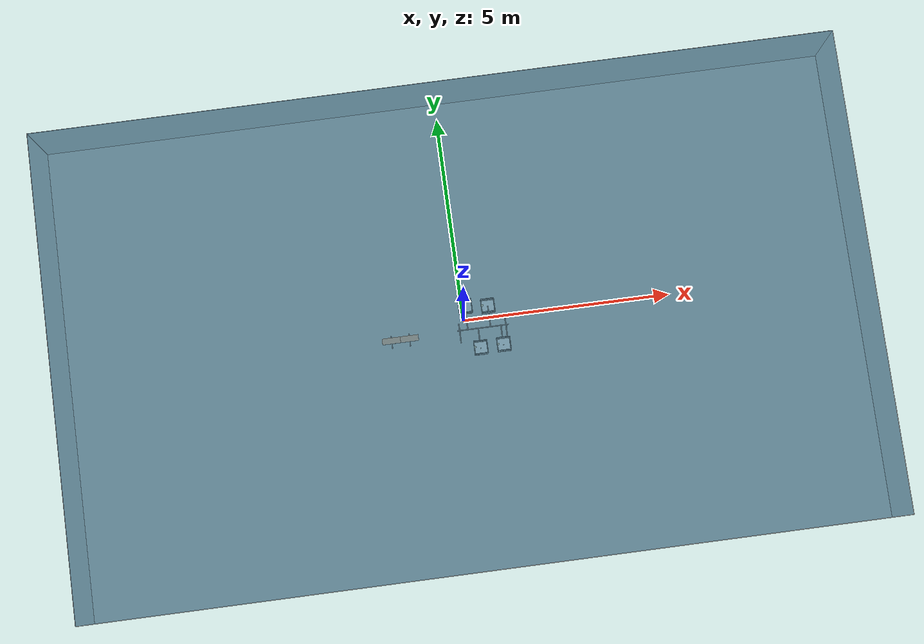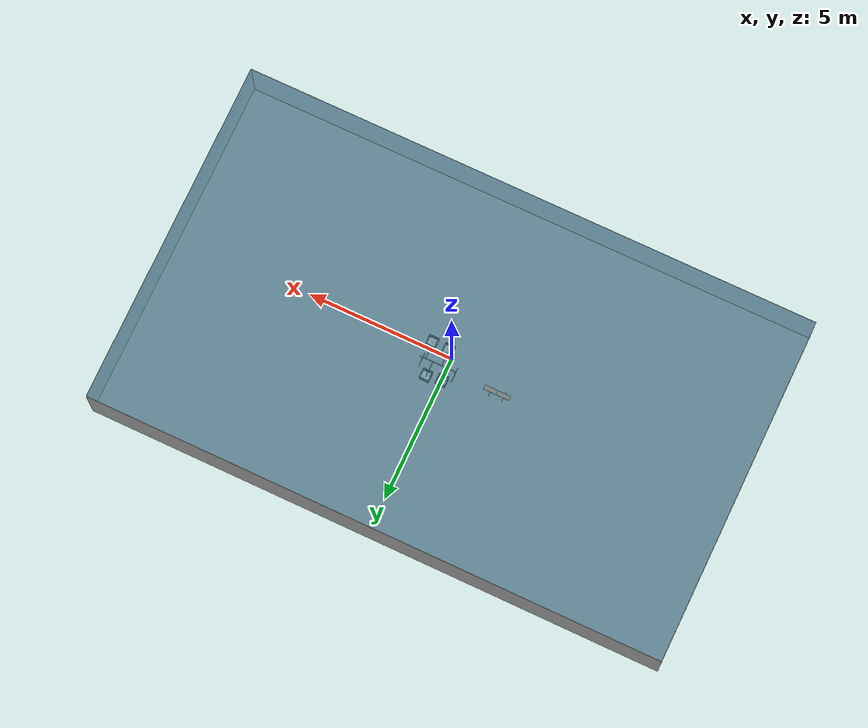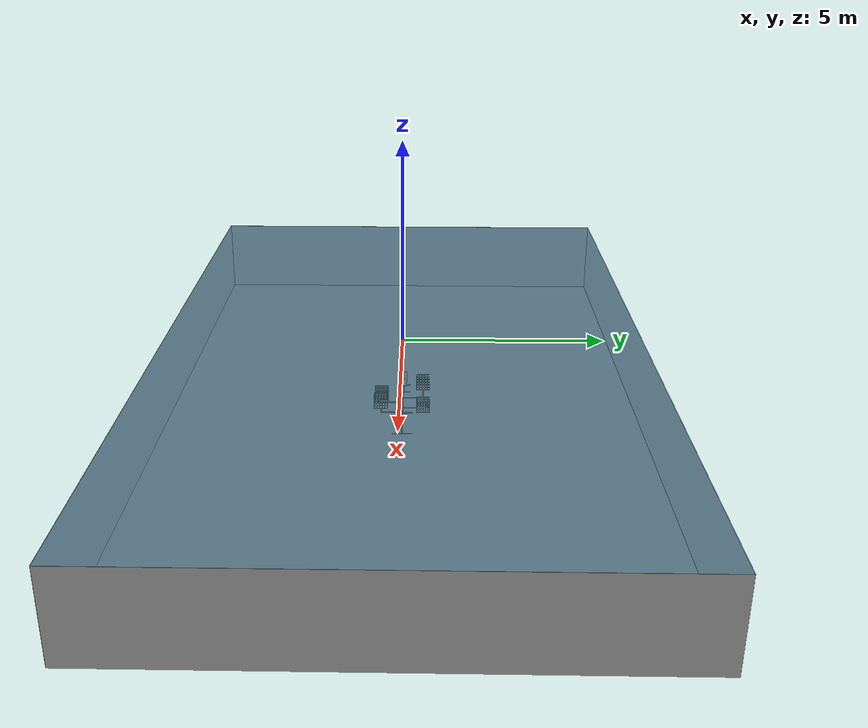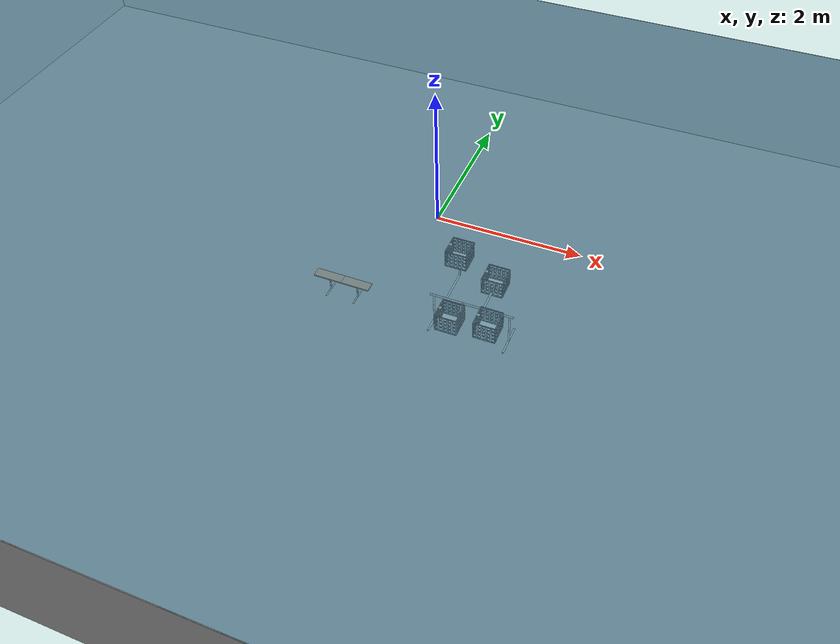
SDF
<sdf version="1.9">
 <world name="rs_task_bins">
  <plugin filename="gz-sim-particle-emitter-system" name="gz::sim::systems::ParticleEmitter"/>
  <plugin filename="gz-sim-physics-system" name="gz::sim::systems::Physics"/>
  <plugin filename="gz-sim-user-commands-system" name="gz::sim::systems::UserCommands"/>
  <plugin filename="gz-sim-scene-broadcaster-system" name="gz::sim::systems::SceneBroadcaster"/>
  <plugin filename="gz-sim-apply-link-wrench-system" name="gz::sim::systems::ApplyLinkWrench"/>
  <plugin filename="gz-sim-imu-system" name="gz::sim::systems::Imu"/>
  <plugin filename="gz-sim-sensors-system" name="gz::sim::systems::Sensors">
   <render_engine>ogre2</render_engine>
  </plugin>
  <plugin filename="gz-sim-dvl-system" name="gz::sim::systems::DopplerVelocityLogSystem"/>
  <plugin filename="gz-sim-buoyancy-system" name="gz::sim::systems::Buoyancy">
   <graded_buoyancy>
    <default_density>1000</default_density>
    <density_change><above_depth>0</above_depth><density>1</density></density_change>
   </graded_buoyancy>
   <enable>duburi</enable>
   <enable>payload_shot_0</enable>
   <enable>payload_shot_1</enable>
   <enable>payload_shot_2</enable>
   <enable>payload_shot_3</enable>
   <enable>payload_shot_4</enable>
   <enable>payload_shot_5</enable>
   <enable>payload_shot_6</enable>
   <enable>payload_shot_7</enable>
   <enable>payload_shot_8</enable>
   <enable>payload_shot_9</enable>
   <enable>payload_shot_10</enable>
   <enable>payload_shot_11</enable>
  </plugin>
  <physics name="default" type="dart">
   <max_step_size>0.001</max_step_size>
   <real_time_factor>1.0</real_time_factor>
   <real_time_update_rate>1000</real_time_update_rate>
   <dart>
    <collision_detector>bullet</collision_detector>
    <solver><solver_type>dantzig</solver_type></solver>
   </dart>
  </physics>
  <gravity>0 0 -9.81</gravity>
  <magnetic_field>3.9e-05 1.1e-06 2.6e-05</magnetic_field>
  <atmosphere type="adiabatic"/>
  <scene>
   <ambient>0.28 0.4 0.48 1</ambient>
   <background>0.08 0.26 0.4 1</background>
   <shadows>true</shadows>
   <fog>
    <color>0.14 0.34 0.42 1</color>
    <type>linear</type>
    <start>1.2</start>
    <end>22.0</end>
    <density>0.028</density>
   </fog>
  </scene>
  <light type="directional" name="sun">
   <pose>0 0 10 0 0 0</pose>
   <diffuse>0.48 0.52 0.56 1</diffuse>
   <specular>0.10 0.10 0.11 1</specular>
   <direction>-0.4 0.15 -0.9</direction>
  </light>
  <light type="directional" name="fill">
   <cast_shadows>false</cast_shadows>
   <pose>0 0 5 0 0 0</pose>
   <diffuse>0.22 0.28 0.34 1</diffuse>
   <specular>0.04 0.05 0.06 1</specular>
   <direction>0.3 -0.2 -1</direction>
  </light>
  <light type="directional" name="caustic_fill">
   <cast_shadows>false</cast_shadows>
   <pose>0 0 3 0 0 0</pose>
   <diffuse>0.12 0.22 0.26 1</diffuse>
   <specular>0.02 0.03 0.04 1</specular>
   <direction>0.1 0.35 -0.85</direction>
  </light>
  <model name="robosub_pool">
   <static>true</static>
   <link name="floor">
    <pose>0 0 -2.1 0 0 0</pose>
    <inertial>
     <mass>1000</mass>
     <inertia><ixx>1000</ixx><ixy>0</ixy><ixz>0</ixz><iyy>1000</iyy><iyz>0</iyz><izz>1000</izz></inertia>
    </inertial>
    <visual name="floor_visual">
     <pose>0 0 0.005 0 0 0</pose>
     <geometry><box><size>20 12 0.01</size></box></geometry>
     <material>
      <ambient>0.55 0.55 0.55 1</ambient>
      <diffuse>0.55 0.55 0.55 1</diffuse>
      <specular>0.08 0.08 0.08 1</specular>
      <emissive>0 0 0 1</emissive>
      <pbr>
       <metal>
        <albedo_map>model://robosub_textures/pool_floor.png</albedo_map>
        <metalness>0.0</metalness>
        <roughness>0.85</roughness>
       </metal>
      </pbr>
     </material>
    </visual>
    <collision name="floor_collision">
     <pose>0 0 -0.05 0 0 0</pose>
     <geometry><box><size>20 12 0.1</size></box></geometry>
    </collision>
   </link>
   <link name="wall_x_pos">
    <inertial>
     <mass>1000</mass>
     <inertia><ixx>1000</ixx><ixy>0</ixy><ixz>0</ixz><iyy>1000</iyy><iyz>0</iyz><izz>1000</izz></inertia>
    </inertial>
    <visual name="wall_x_pos_visual">
     <pose>10 0 -1.05 0 0 0</pose>
     <geometry><box><size>0.01 12 2.1</size></box></geometry>
     <material>
      <ambient>0.55 0.55 0.55 1</ambient>
      <diffuse>0.55 0.55 0.55 1</diffuse>
      <specular>0.08 0.08 0.08 1</specular>
      <emissive>0 0 0 1</emissive>
      <pbr>
       <metal>
        <albedo_map>model://robosub_textures/pool_wall_long.png</albedo_map>
        <metalness>0.0</metalness>
        <roughness>0.85</roughness>
       </metal>
      </pbr>
     </material>
    </visual>
    <collision name="wall_x_pos_collision">
     <pose>10.105 0 -1.05 0 0 0</pose>
     <geometry><box><size>0.2 12.4 2.1</size></box></geometry>
    </collision>
   </link>
   <link name="wall_x_neg">
    <inertial>
     <mass>1000</mass>
     <inertia><ixx>1000</ixx><ixy>0</ixy><ixz>0</ixz><iyy>1000</iyy><iyz>0</iyz><izz>1000</izz></inertia>
    </inertial>
    <visual name="wall_x_neg_visual">
     <pose>-10 0 -1.05 0 0 0</pose>
     <geometry><box><size>0.01 12 2.1</size></box></geometry>
     <material>
      <ambient>0.55 0.55 0.55 1</ambient>
      <diffuse>0.55 0.55 0.55 1</diffuse>
      <specular>0.08 0.08 0.08 1</specular>
      <emissive>0 0 0 1</emissive>
      <pbr>
       <metal>
        <albedo_map>model://robosub_textures/pool_wall_long.png</albedo_map>
        <metalness>0.0</metalness>
        <roughness>0.85</roughness>
       </metal>
      </pbr>
     </material>
    </visual>
    <collision name="wall_x_neg_collision">
     <pose>-10.105 0 -1.05 0 0 0</pose>
     <geometry><box><size>0.2 12.4 2.1</size></box></geometry>
    </collision>
   </link>
   <link name="wall_y_pos">
    <inertial>
     <mass>1000</mass>
     <inertia><ixx>1000</ixx><ixy>0</ixy><ixz>0</ixz><iyy>1000</iyy><iyz>0</iyz><izz>1000</izz></inertia>
    </inertial>
    <visual name="wall_y_pos_visual">
     <pose>0 6 -1.05 0 0 0</pose>
     <geometry><box><size>20 0.01 2.1</size></box></geometry>
     <material>
      <ambient>0.55 0.55 0.55 1</ambient>
      <diffuse>0.55 0.55 0.55 1</diffuse>
      <specular>0.08 0.08 0.08 1</specular>
      <emissive>0 0 0 1</emissive>
      <pbr>
       <metal>
        <albedo_map>model://robosub_textures/pool_wall_short.png</albedo_map>
        <metalness>0.0</metalness>
        <roughness>0.85</roughness>
       </metal>
      </pbr>
     </material>
    </visual>
    <collision name="wall_y_pos_collision">
     <pose>0 6.105 -1.05 0 0 0</pose>
     <geometry><box><size>20 0.2 2.1</size></box></geometry>
    </collision>
   </link>
   <link name="wall_y_neg">
    <inertial>
     <mass>1000</mass>
     <inertia><ixx>1000</ixx><ixy>0</ixy><ixz>0</ixz><iyy>1000</iyy><iyz>0</iyz><izz>1000</izz></inertia>
    </inertial>
    <visual name="wall_y_neg_visual">
     <pose>0 -6 -1.05 0 0 0</pose>
     <geometry><box><size>20 0.01 2.1</size></box></geometry>
     <material>
      <ambient>0.55 0.55 0.55 1</ambient>
      <diffuse>0.55 0.55 0.55 1</diffuse>
      <specular>0.08 0.08 0.08 1</specular>
      <emissive>0 0 0 1</emissive>
      <pbr>
       <metal>
        <albedo_map>model://robosub_textures/pool_wall_short.png</albedo_map>
        <metalness>0.0</metalness>
        <roughness>0.85</roughness>
       </metal>
      </pbr>
     </material>
    </visual>
    <collision name="wall_y_neg_collision">
     <pose>0 -6.105 -1.05 0 0 0</pose>
     <geometry><box><size>20 0.2 2.1</size></box></geometry>
    </collision>
   </link>
   <link name="water_surface">
    <inertial>
     <mass>1</mass>
     <inertia><ixx>1</ixx><ixy>0</ixy><ixz>0</ixz><iyy>1</iyy><iyz>0</iyz><izz>1</izz></inertia>
    </inertial>
    <visual name="water_surface_visual">
     <cast_shadows>false</cast_shadows>
     <transparency>0.18</transparency>
     <geometry><mesh><uri>model://robosub_meshes/meshes/water_robosub.obj</uri></mesh></geometry>
     <material>
      <ambient>0.42 0.6 0.68 1</ambient>
      <diffuse>0.42 0.6 0.68 1</diffuse>
      <specular>0.35 0.35 0.35 1</specular>
      <emissive>0.1 0.1 0.1 1</emissive>
      <pbr>
       <metal>
        <albedo_map>model://robosub_textures/water_surface.png</albedo_map>
        <metalness>0.0</metalness>
        <roughness>0.15</roughness>
       </metal>
      </pbr>
     </material>
    </visual>
   </link>
  </model>
  <model name="marine_snow">
   <static>true</static>
   <pose>0 0 -1.05 0 0 0</pose>
   <link name="link">
    <particle_emitter name="snow" type="box">
     <emitting>true</emitting>
     <size>12 12 2.1</size>
     <particle_size>0.006 0.006 0.006</particle_size>
     <lifetime>30</lifetime>
     <min_velocity>0.004</min_velocity>
     <max_velocity>0.025</max_velocity>
     <scale_rate>0</scale_rate>
     <rate>900</rate>
     <topic>marine_snow</topic>
     <material>
      <diffuse>0.80 0.84 0.80</diffuse>
      <specular>0.05 0.05 0.05</specular>
      <pbr><metal><albedo_map>model://robosub_textures/marine_snow.png</albedo_map></metal></pbr>
     </material>
    </particle_emitter>
   </link>
  </model>
  <include><uri>model://robosub_bins</uri><name>bins</name><pose>0.5 0 -2.1 0 0 0</pose></include>
  <include><uri>model://robosub_path_marker</uri><name>path_in</name><pose>-1.6 0 -2.1 0 0 0</pose></include>
 </world>
</sdf>

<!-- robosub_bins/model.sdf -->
<sdf version="1.9">
  <model name="robosub_bins">
    <static>true</static>
    <plugin filename="gz-sim-label-system" name="gz::sim::systems::Label">
      <label>14</label>
    </plugin>
    <link name="spine">
      <pose>0 0 0.55 0 1.5708 0</pose>
      <inertial>
        <pose>0 0 0 0 0 0</pose>
        <mass>1</mass>
        <inertia>
          <ixx>0.140878</ixx><ixy>0</ixy><ixz>0</ixz>
          <iyy>0.140878</iyy><iyz>0</iyz>
          <izz>8.8445e-05</izz>
        </inertia>
      </inertial>
      <visual name="spine_visual">
        <pose>0 0 0 0 0 0</pose>
        <geometry><cylinder><radius>0.0133</radius><length>1.3</length></cylinder></geometry>
        <material>
          <ambient>0.92 0.92 0.92 1</ambient>
          <diffuse>0.92 0.92 0.92 1</diffuse>
          <specular>0.55 0.55 0.55 1</specular>
          <emissive>0.258 0.258 0.258 1</emissive>
          <pbr>
            <metal>
              <albedo_map>model://robosub_textures/rough_pvc.png</albedo_map>
              <metalness>0.0</metalness>
              <roughness_map>model://robosub_textures/rough_pvc.png</roughness_map>
              <normal_map>model://robosub_textures/norm_pvc.png</normal_map>
            </metal>
          </pbr>
        </material>
      </visual>
      <collision name="spine_collision">
        <pose>0 0 0 0 0 0</pose>
        <geometry><cylinder><radius>0.0133</radius><length>1.3</length></cylinder></geometry>
      </collision>
    </link>
    <link name="foot_riser_0">
      <pose>-0.590909 0 0.275 0 0 0</pose>
      <inertial>
        <pose>0 0 0 0 0 0</pose>
        <mass>1</mass>
        <inertia>
          <ixx>0.0252526</ixx><ixy>0</ixy><ixz>0</ixz>
          <iyy>0.0252526</iyy><iyz>0</iyz>
          <izz>8.8445e-05</izz>
        </inertia>
      </inertial>
      <visual name="foot_riser_0_visual">
        <pose>0 0 0 0 0 0</pose>
        <geometry><cylinder><radius>0.0133</radius><length>0.55</length></cylinder></geometry>
        <material>
          <ambient>0.92 0.92 0.92 1</ambient>
          <diffuse>0.92 0.92 0.92 1</diffuse>
          <specular>0.55 0.55 0.55 1</specular>
          <emissive>0.258 0.258 0.258 1</emissive>
          <pbr>
            <metal>
              <albedo_map>model://robosub_textures/rough_pvc.png</albedo_map>
              <metalness>0.0</metalness>
              <roughness_map>model://robosub_textures/rough_pvc.png</roughness_map>
              <normal_map>model://robosub_textures/norm_pvc.png</normal_map>
            </metal>
          </pbr>
        </material>
      </visual>
      <collision name="foot_riser_0_collision">
        <pose>0 0 0 0 0 0</pose>
        <geometry><cylinder><radius>0.0133</radius><length>0.55</length></cylinder></geometry>
      </collision>
    </link>
    <link name="foot_0">
      <pose>-0.590909 0 0.03 1.5708 0 0</pose>
      <inertial>
        <pose>0 0 0 0 0 0</pose>
        <mass>1</mass>
        <inertia>
          <ixx>0.0208776</ixx><ixy>0</ixy><ixz>0</ixz>
          <iyy>0.0208776</iyy><iyz>0</iyz>
          <izz>8.8445e-05</izz>
        </inertia>
      </inertial>
      <visual name="foot_0_visual">
        <pose>0 0 0 0 0 0</pose>
        <geometry><cylinder><radius>0.0133</radius><length>0.5</length></cylinder></geometry>
        <material>
          <ambient>0.92 0.92 0.92 1</ambient>
          <diffuse>0.92 0.92 0.92 1</diffuse>
          <specular>0.55 0.55 0.55 1</specular>
          <emissive>0.258 0.258 0.258 1</emissive>
          <pbr>
            <metal>
              <albedo_map>model://robosub_textures/rough_pvc.png</albedo_map>
              <metalness>0.0</metalness>
              <roughness_map>model://robosub_textures/rough_pvc.png</roughness_map>
              <normal_map>model://robosub_textures/norm_pvc.png</normal_map>
            </metal>
          </pbr>
        </material>
      </visual>
      <collision name="foot_0_collision">
        <pose>0 0 0 0 0 0</pose>
        <geometry><cylinder><radius>0.0133</radius><length>0.5</length></cylinder></geometry>
      </collision>
    </link>
    <link name="foot_riser_1">
      <pose>0.590909 0 0.275 0 0 0</pose>
      <inertial>
        <pose>0 0 0 0 0 0</pose>
        <mass>1</mass>
        <inertia>
          <ixx>0.0252526</ixx><ixy>0</ixy><ixz>0</ixz>
          <iyy>0.0252526</iyy><iyz>0</iyz>
          <izz>8.8445e-05</izz>
        </inertia>
      </inertial>
      <visual name="foot_riser_1_visual">
        <pose>0 0 0 0 0 0</pose>
        <geometry><cylinder><radius>0.0133</radius><length>0.55</length></cylinder></geometry>
        <material>
          <ambient>0.92 0.92 0.92 1</ambient>
          <diffuse>0.92 0.92 0.92 1</diffuse>
          <specular>0.55 0.55 0.55 1</specular>
          <emissive>0.258 0.258 0.258 1</emissive>
          <pbr>
            <metal>
              <albedo_map>model://robosub_textures/rough_pvc.png</albedo_map>
              <metalness>0.0</metalness>
              <roughness_map>model://robosub_textures/rough_pvc.png</roughness_map>
              <normal_map>model://robosub_textures/norm_pvc.png</normal_map>
            </metal>
          </pbr>
        </material>
      </visual>
      <collision name="foot_riser_1_collision">
        <pose>0 0 0 0 0 0</pose>
        <geometry><cylinder><radius>0.0133</radius><length>0.55</length></cylinder></geometry>
      </collision>
    </link>
    <link name="foot_1">
      <pose>0.590909 0 0.03 1.5708 0 0</pose>
      <inertial>
        <pose>0 0 0 0 0 0</pose>
        <mass>1</mass>
        <inertia>
          <ixx>0.0208776</ixx><ixy>0</ixy><ixz>0</ixz>
          <iyy>0.0208776</iyy><iyz>0</iyz>
          <izz>8.8445e-05</izz>
        </inertia>
      </inertial>
      <visual name="foot_1_visual">
        <pose>0 0 0 0 0 0</pose>
        <geometry><cylinder><radius>0.0133</radius><length>0.5</length></cylinder></geometry>
        <material>
          <ambient>0.92 0.92 0.92 1</ambient>
          <diffuse>0.92 0.92 0.92 1</diffuse>
          <specular>0.55 0.55 0.55 1</specular>
          <emissive>0.258 0.258 0.258 1</emissive>
          <pbr>
            <metal>
              <albedo_map>model://robosub_textures/rough_pvc.png</albedo_map>
              <metalness>0.0</metalness>
              <roughness_map>model://robosub_textures/rough_pvc.png</roughness_map>
              <normal_map>model://robosub_textures/norm_pvc.png</normal_map>
            </metal>
          </pbr>
        </material>
      </visual>
      <collision name="foot_1_collision">
        <pose>0 0 0 0 0 0</pose>
        <geometry><cylinder><radius>0.0133</radius><length>0.5</length></cylinder></geometry>
      </collision>
    </link>
    <link name="arm_sr_a">
      <pose>-0.39 0.26 0.55 1.5708 0 0</pose>
      <inertial>
        <pose>0 0 0 0 0 0</pose>
        <mass>1</mass>
        <inertia>
          <ixx>0.0225776</ixx><ixy>0</ixy><ixz>0</ixz>
          <iyy>0.0225776</iyy><iyz>0</iyz>
          <izz>8.8445e-05</izz>
        </inertia>
      </inertial>
      <visual name="arm_sr_a_visual">
        <pose>0 0 0 0 0 0</pose>
        <geometry><cylinder><radius>0.0133</radius><length>0.52</length></cylinder></geometry>
        <material>
          <ambient>0.92 0.92 0.92 1</ambient>
          <diffuse>0.92 0.92 0.92 1</diffuse>
          <specular>0.55 0.55 0.55 1</specular>
          <emissive>0.258 0.258 0.258 1</emissive>
          <pbr>
            <metal>
              <albedo_map>model://robosub_textures/rough_pvc.png</albedo_map>
              <metalness>0.0</metalness>
              <roughness_map>model://robosub_textures/rough_pvc.png</roughness_map>
              <normal_map>model://robosub_textures/norm_pvc.png</normal_map>
            </metal>
          </pbr>
        </material>
      </visual>
      <collision name="arm_sr_a_collision">
        <pose>0 0 0 0 0 0</pose>
        <geometry><cylinder><radius>0.0133</radius><length>0.52</length></cylinder></geometry>
      </collision>
    </link>
    <link name="riser_sr_a">
      <pose>-0.39 0.52 0.7 0 0 0</pose>
      <inertial>
        <pose>0 0 0 0 0 0</pose>
        <mass>1</mass>
        <inertia>
          <ixx>0.00857756</ixx><ixy>0</ixy><ixz>0</ixz>
          <iyy>0.00857756</iyy><iyz>0</iyz>
          <izz>8.8445e-05</izz>
        </inertia>
      </inertial>
      <visual name="riser_sr_a_visual">
        <pose>0 0 0 0 0 0</pose>
        <geometry><cylinder><radius>0.0133</radius><length>0.32</length></cylinder></geometry>
        <material>
          <ambient>0.92 0.92 0.92 1</ambient>
          <diffuse>0.92 0.92 0.92 1</diffuse>
          <specular>0.55 0.55 0.55 1</specular>
          <emissive>0.258 0.258 0.258 1</emissive>
          <pbr>
            <metal>
              <albedo_map>model://robosub_textures/rough_pvc.png</albedo_map>
              <metalness>0.0</metalness>
              <roughness_map>model://robosub_textures/rough_pvc.png</roughness_map>
              <normal_map>model://robosub_textures/norm_pvc.png</normal_map>
            </metal>
          </pbr>
        </material>
      </visual>
      <collision name="riser_sr_a_collision">
        <pose>0 0 0 0 0 0</pose>
        <geometry><cylinder><radius>0.0133</radius><length>0.32</length></cylinder></geometry>
      </collision>
    </link>
    <link name="crate_sr_a_floor">
      <pose>-0.39 0.52 0.85 0 0 0</pose>
      <inertial>
        <pose>0 0 0 0 0 0</pose>
        <mass>1</mass>
        <inertia>
          <ixx>0.00936408</ixx><ixy>0</ixy><ixz>0</ixz>
          <iyy>0.00936408</iyy><iyz>0</iyz>
          <izz>0.0187042</izz>
        </inertia>
      </inertial>
      <visual name="crate_sr_a_floor_visual">
        <pose>0 0 0 0 0 0</pose>
        <geometry><box><size>0.335 0.335 0.012</size></box></geometry>
        <material>
          <ambient>1 1 1 1</ambient>
          <diffuse>1 1 1 1</diffuse>
          <specular>0.06 0.06 0.06 1</specular>
          <emissive>0.1 0.1 0.1 1</emissive>
          <pbr>
            <metal>
              <albedo_map>model://robosub_textures/role_fire.png</albedo_map>
              <metalness>0.0</metalness>
              <roughness>0.55</roughness>
            </metal>
          </pbr>
        </material>
      </visual>
      <collision name="crate_sr_a_floor_collision">
        <pose>0 0 0 0 0 0</pose>
        <geometry><box><size>0.335 0.335 0.012</size></box></geometry>
      </collision>
    </link>
    <link name="crate_sr_a_xp">
      <pose>-0.2285 0.52 0.99 0 0 0</pose>
      <inertial>
        <pose>0 0 0 0 0 0</pose>
        <mass>0.5</mass>
        <inertia>
          <ixx>0.00794271</ixx><ixy>0</ixy><ixz>0</ixz>
          <iyy>0.00327267</iyy><iyz>0</iyz>
          <izz>0.00468204</izz>
        </inertia>
      </inertial>
      <visual name="crate_sr_a_xp_visual">
        <pose>0 0 0 0 0 0</pose>
        <geometry><mesh><uri>model://robosub_meshes/meshes/crate_wall.obj</uri></mesh></geometry>
        <material>
          <ambient>0.18 0.18 0.2 1</ambient>
          <diffuse>0.18 0.18 0.2 1</diffuse>
          <specular>0.14 0.14 0.14 1</specular>
          <emissive>0.04 0.04 0.04 1</emissive>
          <pbr>
            <metal>
              <albedo_map>model://robosub_textures/rough_plastic.png</albedo_map>
              <metalness>0.0</metalness>
              <roughness_map>model://robosub_textures/rough_plastic.png</roughness_map>
              <normal_map>model://robosub_textures/norm_plastic.png</normal_map>
              <double_sided>true</double_sided>
            </metal>
          </pbr>
        </material>
      </visual>
      <collision name="crate_sr_a_xp_collision">
        <pose>0 0 0 0 0 0</pose>
        <geometry><box><size>0.012 0.335 0.28</size></box></geometry>
      </collision>
    </link>
    <link name="crate_sr_a_xn">
      <pose>-0.5515 0.52 0.99 0 0 0</pose>
      <inertial>
        <pose>0 0 0 0 0 0</pose>
        <mass>0.5</mass>
        <inertia>
          <ixx>0.00794271</ixx><ixy>0</ixy><ixz>0</ixz>
          <iyy>0.00327267</iyy><iyz>0</iyz>
          <izz>0.00468204</izz>
        </inertia>
      </inertial>
      <visual name="crate_sr_a_xn_visual">
        <pose>0 0 0 0 0 0</pose>
        <geometry><mesh><uri>model://robosub_meshes/meshes/crate_wall.obj</uri></mesh></geometry>
        <material>
          <ambient>0.18 0.18 0.2 1</ambient>
          <diffuse>0.18 0.18 0.2 1</diffuse>
          <specular>0.14 0.14 0.14 1</specular>
          <emissive>0.04 0.04 0.04 1</emissive>
          <pbr>
            <metal>
              <albedo_map>model://robosub_textures/rough_plastic.png</albedo_map>
              <metalness>0.0</metalness>
              <roughness_map>model://robosub_textures/rough_plastic.png</roughness_map>
              <normal_map>model://robosub_textures/norm_plastic.png</normal_map>
              <double_sided>true</double_sided>
            </metal>
          </pbr>
        </material>
      </visual>
      <collision name="crate_sr_a_xn_collision">
        <pose>0 0 0 0 0 0</pose>
        <geometry><box><size>0.012 0.335 0.28</size></box></geometry>
      </collision>
    </link>
    <link name="crate_sr_a_yp">
      <pose>-0.39 0.6815 0.99 0 0 1.5708</pose>
      <inertial>
        <pose>0 0 0 0 0 0</pose>
        <mass>0.5</mass>
        <inertia>
          <ixx>0.00327267</ixx><ixy>0</ixy><ixz>0</ixz>
          <iyy>0.00794271</iyy><iyz>0</iyz>
          <izz>0.00468204</izz>
        </inertia>
      </inertial>
      <visual name="crate_sr_a_yp_visual">
        <pose>0 0 0 0 0 0</pose>
        <geometry><mesh><uri>model://robosub_meshes/meshes/crate_wall.obj</uri></mesh></geometry>
        <material>
          <ambient>0.18 0.18 0.2 1</ambient>
          <diffuse>0.18 0.18 0.2 1</diffuse>
          <specular>0.14 0.14 0.14 1</specular>
          <emissive>0.04 0.04 0.04 1</emissive>
          <pbr>
            <metal>
              <albedo_map>model://robosub_textures/rough_plastic.png</albedo_map>
              <metalness>0.0</metalness>
              <roughness_map>model://robosub_textures/rough_plastic.png</roughness_map>
              <normal_map>model://robosub_textures/norm_plastic.png</normal_map>
              <double_sided>true</double_sided>
            </metal>
          </pbr>
        </material>
      </visual>
      <collision name="crate_sr_a_yp_collision">
        <pose>0 0 0 0 0 0</pose>
        <geometry><box><size>0.335 0.012 0.28</size></box></geometry>
      </collision>
    </link>
    <link name="crate_sr_a_yn">
      <pose>-0.39 0.3585 0.99 0 0 1.5708</pose>
      <inertial>
        <pose>0 0 0 0 0 0</pose>
        <mass>0.5</mass>
        <inertia>
          <ixx>0.00327267</ixx><ixy>0</ixy><ixz>0</ixz>
          <iyy>0.00794271</iyy><iyz>0</iyz>
          <izz>0.00468204</izz>
        </inertia>
      </inertial>
      <visual name="crate_sr_a_yn_visual">
        <pose>0 0 0 0 0 0</pose>
        <geometry><mesh><uri>model://robosub_meshes/meshes/crate_wall.obj</uri></mesh></geometry>
        <material>
          <ambient>0.18 0.18 0.2 1</ambient>
          <diffuse>0.18 0.18 0.2 1</diffuse>
          <specular>0.14 0.14 0.14 1</specular>
          <emissive>0.04 0.04 0.04 1</emissive>
          <pbr>
            <metal>
              <albedo_map>model://robosub_textures/rough_plastic.png</albedo_map>
              <metalness>0.0</metalness>
              <roughness_map>model://robosub_textures/rough_plastic.png</roughness_map>
              <normal_map>model://robosub_textures/norm_plastic.png</normal_map>
              <double_sided>true</double_sided>
            </metal>
          </pbr>
        </material>
      </visual>
      <collision name="crate_sr_a_yn_collision">
        <pose>0 0 0 0 0 0</pose>
        <geometry><box><size>0.335 0.012 0.28</size></box></geometry>
      </collision>
    </link>
    <link name="light_sr_a">
      <pose>-0.5309 0.52 1.13 0 0 0</pose>
      <inertial>
        <pose>0 0 0 0 0 0</pose>
        <mass>0.05</mass>
        <inertia>
          <ixx>8.79883e-06</ixx><ixy>0</ixy><ixz>0</ixz>
          <iyy>8.79883e-06</iyy><iyz>0</iyz>
          <izz>1.59643e-05</izz>
        </inertia>
      </inertial>
      <visual name="light_sr_a_visual">
        <pose>0 0 0 0 0 0</pose>
        <geometry><cylinder><radius>0.02527</radius><length>0.014</length></cylinder></geometry>
        <material>
          <ambient>1 0.92 0.55 1</ambient>
          <diffuse>1 0.92 0.55 1</diffuse>
          <specular>0.2 0.2 0.2 1</specular>
          <emissive>0.85 0.782 0.4675 1</emissive>
        </material>
      </visual>
    </link>
    <link name="arm_rescue_a">
      <pose>-0.13 -0.26 0.55 1.5708 0 0</pose>
      <inertial>
        <pose>0 0 0 0 0 0</pose>
        <mass>1</mass>
        <inertia>
          <ixx>0.0225776</ixx><ixy>0</ixy><ixz>0</ixz>
          <iyy>0.0225776</iyy><iyz>0</iyz>
          <izz>8.8445e-05</izz>
        </inertia>
      </inertial>
      <visual name="arm_rescue_a_visual">
        <pose>0 0 0 0 0 0</pose>
        <geometry><cylinder><radius>0.0133</radius><length>0.52</length></cylinder></geometry>
        <material>
          <ambient>0.92 0.92 0.92 1</ambient>
          <diffuse>0.92 0.92 0.92 1</diffuse>
          <specular>0.55 0.55 0.55 1</specular>
          <emissive>0.258 0.258 0.258 1</emissive>
          <pbr>
            <metal>
              <albedo_map>model://robosub_textures/rough_pvc.png</albedo_map>
              <metalness>0.0</metalness>
              <roughness_map>model://robosub_textures/rough_pvc.png</roughness_map>
              <normal_map>model://robosub_textures/norm_pvc.png</normal_map>
            </metal>
          </pbr>
        </material>
      </visual>
      <collision name="arm_rescue_a_collision">
        <pose>0 0 0 0 0 0</pose>
        <geometry><cylinder><radius>0.0133</radius><length>0.52</length></cylinder></geometry>
      </collision>
    </link>
    <link name="riser_rescue_a">
      <pose>-0.13 -0.52 0.6 0 0 0</pose>
      <inertial>
        <pose>0 0 0 0 0 0</pose>
        <mass>1</mass>
        <inertia>
          <ixx>0.00124422</ixx><ixy>0</ixy><ixz>0</ixz>
          <iyy>0.00124422</iyy><iyz>0</iyz>
          <izz>8.8445e-05</izz>
        </inertia>
      </inertial>
      <visual name="riser_rescue_a_visual">
        <pose>0 0 0 0 0 0</pose>
        <geometry><cylinder><radius>0.0133</radius><length>0.12</length></cylinder></geometry>
        <material>
          <ambient>0.92 0.92 0.92 1</ambient>
          <diffuse>0.92 0.92 0.92 1</diffuse>
          <specular>0.55 0.55 0.55 1</specular>
          <emissive>0.258 0.258 0.258 1</emissive>
          <pbr>
            <metal>
              <albedo_map>model://robosub_textures/rough_pvc.png</albedo_map>
              <metalness>0.0</metalness>
              <roughness_map>model://robosub_textures/rough_pvc.png</roughness_map>
              <normal_map>model://robosub_textures/norm_pvc.png</normal_map>
            </metal>
          </pbr>
        </material>
      </visual>
      <collision name="riser_rescue_a_collision">
        <pose>0 0 0 0 0 0</pose>
        <geometry><cylinder><radius>0.0133</radius><length>0.12</length></cylinder></geometry>
      </collision>
    </link>
    <link name="crate_rescue_a_floor">
      <pose>-0.13 -0.52 0.65 0 0 0</pose>
      <inertial>
        <pose>0 0 0 0 0 0</pose>
        <mass>1</mass>
        <inertia>
          <ixx>0.00936408</ixx><ixy>0</ixy><ixz>0</ixz>
          <iyy>0.00936408</iyy><iyz>0</iyz>
          <izz>0.0187042</izz>
        </inertia>
      </inertial>
      <visual name="crate_rescue_a_floor_visual">
        <pose>0 0 0 0 0 0</pose>
        <geometry><box><size>0.335 0.335 0.012</size></box></geometry>
        <material>
          <ambient>1 1 1 1</ambient>
          <diffuse>1 1 1 1</diffuse>
          <specular>0.06 0.06 0.06 1</specular>
          <emissive>0.1 0.1 0.1 1</emissive>
          <pbr>
            <metal>
              <albedo_map>model://robosub_textures/role_droplet.png</albedo_map>
              <metalness>0.0</metalness>
              <roughness>0.55</roughness>
            </metal>
          </pbr>
        </material>
      </visual>
      <collision name="crate_rescue_a_floor_collision">
        <pose>0 0 0 0 0 0</pose>
        <geometry><box><size>0.335 0.335 0.012</size></box></geometry>
      </collision>
    </link>
    <link name="crate_rescue_a_xp">
      <pose>0.0315 -0.52 0.79 0 0 0</pose>
      <inertial>
        <pose>0 0 0 0 0 0</pose>
        <mass>0.5</mass>
        <inertia>
          <ixx>0.00794271</ixx><ixy>0</ixy><ixz>0</ixz>
          <iyy>0.00327267</iyy><iyz>0</iyz>
          <izz>0.00468204</izz>
        </inertia>
      </inertial>
      <visual name="crate_rescue_a_xp_visual">
        <pose>0 0 0 0 0 0</pose>
        <geometry><mesh><uri>model://robosub_meshes/meshes/crate_wall.obj</uri></mesh></geometry>
        <material>
          <ambient>0.18 0.18 0.2 1</ambient>
          <diffuse>0.18 0.18 0.2 1</diffuse>
          <specular>0.14 0.14 0.14 1</specular>
          <emissive>0.04 0.04 0.04 1</emissive>
          <pbr>
            <metal>
              <albedo_map>model://robosub_textures/rough_plastic.png</albedo_map>
              <metalness>0.0</metalness>
              <roughness_map>model://robosub_textures/rough_plastic.png</roughness_map>
              <normal_map>model://robosub_textures/norm_plastic.png</normal_map>
              <double_sided>true</double_sided>
            </metal>
          </pbr>
        </material>
      </visual>
      <collision name="crate_rescue_a_xp_collision">
        <pose>0 0 0 0 0 0</pose>
        <geometry><box><size>0.012 0.335 0.28</size></box></geometry>
      </collision>
    </link>
    <link name="crate_rescue_a_xn">
      <pose>-0.2915 -0.52 0.79 0 0 0</pose>
      <inertial>
        <pose>0 0 0 0 0 0</pose>
        <mass>0.5</mass>
        <inertia>
          <ixx>0.00794271</ixx><ixy>0</ixy><ixz>0</ixz>
          <iyy>0.00327267</iyy><iyz>0</iyz>
          <izz>0.00468204</izz>
        </inertia>
      </inertial>
      <visual name="crate_rescue_a_xn_visual">
        <pose>0 0 0 0 0 0</pose>
        <geometry><mesh><uri>model://robosub_meshes/meshes/crate_wall.obj</uri></mesh></geometry>
        <material>
          <ambient>0.18 0.18 0.2 1</ambient>
          <diffuse>0.18 0.18 0.2 1</diffuse>
          <specular>0.14 0.14 0.14 1</specular>
          <emissive>0.04 0.04 0.04 1</emissive>
          <pbr>
            <metal>
              <albedo_map>model://robosub_textures/rough_plastic.png</albedo_map>
              <metalness>0.0</metalness>
              <roughness_map>model://robosub_textures/rough_plastic.png</roughness_map>
              <normal_map>model://robosub_textures/norm_plastic.png</normal_map>
              <double_sided>true</double_sided>
            </metal>
          </pbr>
        </material>
      </visual>
      <collision name="crate_rescue_a_xn_collision">
        <pose>0 0 0 0 0 0</pose>
        <geometry><box><size>0.012 0.335 0.28</size></box></geometry>
      </collision>
    </link>
    <link name="crate_rescue_a_yp">
      <pose>-0.13 -0.3585 0.79 0 0 1.5708</pose>
      <inertial>
        <pose>0 0 0 0 0 0</pose>
        <mass>0.5</mass>
        <inertia>
          <ixx>0.00327267</ixx><ixy>0</ixy><ixz>0</ixz>
          <iyy>0.00794271</iyy><iyz>0</iyz>
          <izz>0.00468204</izz>
        </inertia>
      </inertial>
      <visual name="crate_rescue_a_yp_visual">
        <pose>0 0 0 0 0 0</pose>
        <geometry><mesh><uri>model://robosub_meshes/meshes/crate_wall.obj</uri></mesh></geometry>
        <material>
          <ambient>0.18 0.18 0.2 1</ambient>
          <diffuse>0.18 0.18 0.2 1</diffuse>
          <specular>0.14 0.14 0.14 1</specular>
          <emissive>0.04 0.04 0.04 1</emissive>
          <pbr>
            <metal>
              <albedo_map>model://robosub_textures/rough_plastic.png</albedo_map>
              <metalness>0.0</metalness>
              <roughness_map>model://robosub_textures/rough_plastic.png</roughness_map>
              <normal_map>model://robosub_textures/norm_plastic.png</normal_map>
              <double_sided>true</double_sided>
            </metal>
          </pbr>
        </material>
      </visual>
      <collision name="crate_rescue_a_yp_collision">
        <pose>0 0 0 0 0 0</pose>
        <geometry><box><size>0.335 0.012 0.28</size></box></geometry>
      </collision>
    </link>
    <link name="crate_rescue_a_yn">
      <pose>-0.13 -0.6815 0.79 0 0 1.5708</pose>
      <inertial>
        <pose>0 0 0 0 0 0</pose>
        <mass>0.5</mass>
        <inertia>
          <ixx>0.00327267</ixx><ixy>0</ixy><ixz>0</ixz>
          <iyy>0.00794271</iyy><iyz>0</iyz>
          <izz>0.00468204</izz>
        </inertia>
      </inertial>
      <visual name="crate_rescue_a_yn_visual">
        <pose>0 0 0 0 0 0</pose>
        <geometry><mesh><uri>model://robosub_meshes/meshes/crate_wall.obj</uri></mesh></geometry>
        <material>
          <ambient>0.18 0.18 0.2 1</ambient>
          <diffuse>0.18 0.18 0.2 1</diffuse>
          <specular>0.14 0.14 0.14 1</specular>
          <emissive>0.04 0.04 0.04 1</emissive>
          <pbr>
            <metal>
              <albedo_map>model://robosub_textures/rough_plastic.png</albedo_map>
              <metalness>0.0</metalness>
              <roughness_map>model://robosub_textures/rough_plastic.png</roughness_map>
              <normal_map>model://robosub_textures/norm_plastic.png</normal_map>
              <double_sided>true</double_sided>
            </metal>
          </pbr>
        </material>
      </visual>
      <collision name="crate_rescue_a_yn_collision">
        <pose>0 0 0 0 0 0</pose>
        <geometry><box><size>0.335 0.012 0.28</size></box></geometry>
      </collision>
    </link>
    <link name="light_rescue_a">
      <pose>-0.2709 -0.52 0.93 0 0 0</pose>
      <inertial>
        <pose>0 0 0 0 0 0</pose>
        <mass>0.05</mass>
        <inertia>
          <ixx>8.79883e-06</ixx><ixy>0</ixy><ixz>0</ixz>
          <iyy>8.79883e-06</iyy><iyz>0</iyz>
          <izz>1.59643e-05</izz>
        </inertia>
      </inertial>
      <visual name="light_rescue_a_visual">
        <pose>0 0 0 0 0 0</pose>
        <geometry><cylinder><radius>0.02527</radius><length>0.014</length></cylinder></geometry>
        <material>
          <ambient>1 0.92 0.55 1</ambient>
          <diffuse>1 0.92 0.55 1</diffuse>
          <specular>0.2 0.2 0.2 1</specular>
          <emissive>0.85 0.782 0.4675 1</emissive>
        </material>
      </visual>
    </link>
    <link name="arm_sr_b">
      <pose>0.182 0.26 0.55 1.5708 0 0</pose>
      <inertial>
        <pose>0 0 0 0 0 0</pose>
        <mass>1</mass>
        <inertia>
          <ixx>0.0225776</ixx><ixy>0</ixy><ixz>0</ixz>
          <iyy>0.0225776</iyy><iyz>0</iyz>
          <izz>8.8445e-05</izz>
        </inertia>
      </inertial>
      <visual name="arm_sr_b_visual">
        <pose>0 0 0 0 0 0</pose>
        <geometry><cylinder><radius>0.0133</radius><length>0.52</length></cylinder></geometry>
        <material>
          <ambient>0.92 0.92 0.92 1</ambient>
          <diffuse>0.92 0.92 0.92 1</diffuse>
          <specular>0.55 0.55 0.55 1</specular>
          <emissive>0.258 0.258 0.258 1</emissive>
          <pbr>
            <metal>
              <albedo_map>model://robosub_textures/rough_pvc.png</albedo_map>
              <metalness>0.0</metalness>
              <roughness_map>model://robosub_textures/rough_pvc.png</roughness_map>
              <normal_map>model://robosub_textures/norm_pvc.png</normal_map>
            </metal>
          </pbr>
        </material>
      </visual>
      <collision name="arm_sr_b_collision">
        <pose>0 0 0 0 0 0</pose>
        <geometry><cylinder><radius>0.0133</radius><length>0.52</length></cylinder></geometry>
      </collision>
    </link>
    <link name="riser_sr_b">
      <pose>0.182 0.52 0.525 0 0 0</pose>
      <inertial>
        <pose>0 0 0 0 0 0</pose>
        <mass>1</mass>
        <inertia>
          <ixx>0.000452556</ixx><ixy>0</ixy><ixz>0</ixz>
          <iyy>0.000452556</iyy><iyz>0</iyz>
          <izz>8.8445e-05</izz>
        </inertia>
      </inertial>
      <visual name="riser_sr_b_visual">
        <pose>0 0 0 0 0 0</pose>
        <geometry><cylinder><radius>0.0133</radius><length>0.07</length></cylinder></geometry>
        <material>
          <ambient>0.92 0.92 0.92 1</ambient>
          <diffuse>0.92 0.92 0.92 1</diffuse>
          <specular>0.55 0.55 0.55 1</specular>
          <emissive>0.258 0.258 0.258 1</emissive>
          <pbr>
            <metal>
              <albedo_map>model://robosub_textures/rough_pvc.png</albedo_map>
              <metalness>0.0</metalness>
              <roughness_map>model://robosub_textures/rough_pvc.png</roughness_map>
              <normal_map>model://robosub_textures/norm_pvc.png</normal_map>
            </metal>
          </pbr>
        </material>
      </visual>
      <collision name="riser_sr_b_collision">
        <pose>0 0 0 0 0 0</pose>
        <geometry><cylinder><radius>0.0133</radius><length>0.07</length></cylinder></geometry>
      </collision>
    </link>
    <link name="crate_sr_b_floor">
      <pose>0.182 0.52 0.5 0 0 0</pose>
      <inertial>
        <pose>0 0 0 0 0 0</pose>
        <mass>1</mass>
        <inertia>
          <ixx>0.00936408</ixx><ixy>0</ixy><ixz>0</ixz>
          <iyy>0.00936408</iyy><iyz>0</iyz>
          <izz>0.0187042</izz>
        </inertia>
      </inertial>
      <visual name="crate_sr_b_floor_visual">
        <pose>0 0 0 0 0 0</pose>
        <geometry><box><size>0.335 0.335 0.012</size></box></geometry>
        <material>
          <ambient>1 1 1 1</ambient>
          <diffuse>1 1 1 1</diffuse>
          <specular>0.06 0.06 0.06 1</specular>
          <emissive>0.1 0.1 0.1 1</emissive>
          <pbr>
            <metal>
              <albedo_map>model://robosub_textures/role_fire.png</albedo_map>
              <metalness>0.0</metalness>
              <roughness>0.55</roughness>
            </metal>
          </pbr>
        </material>
      </visual>
      <collision name="crate_sr_b_floor_collision">
        <pose>0 0 0 0 0 0</pose>
        <geometry><box><size>0.335 0.335 0.012</size></box></geometry>
      </collision>
    </link>
    <link name="crate_sr_b_xp">
      <pose>0.3435 0.52 0.64 0 0 0</pose>
      <inertial>
        <pose>0 0 0 0 0 0</pose>
        <mass>0.5</mass>
        <inertia>
          <ixx>0.00794271</ixx><ixy>0</ixy><ixz>0</ixz>
          <iyy>0.00327267</iyy><iyz>0</iyz>
          <izz>0.00468204</izz>
        </inertia>
      </inertial>
      <visual name="crate_sr_b_xp_visual">
        <pose>0 0 0 0 0 0</pose>
        <geometry><mesh><uri>model://robosub_meshes/meshes/crate_wall.obj</uri></mesh></geometry>
        <material>
          <ambient>0.18 0.18 0.2 1</ambient>
          <diffuse>0.18 0.18 0.2 1</diffuse>
          <specular>0.14 0.14 0.14 1</specular>
          <emissive>0.04 0.04 0.04 1</emissive>
          <pbr>
            <metal>
              <albedo_map>model://robosub_textures/rough_plastic.png</albedo_map>
              <metalness>0.0</metalness>
              <roughness_map>model://robosub_textures/rough_plastic.png</roughness_map>
              <normal_map>model://robosub_textures/norm_plastic.png</normal_map>
              <double_sided>true</double_sided>
            </metal>
          </pbr>
        </material>
      </visual>
      <collision name="crate_sr_b_xp_collision">
        <pose>0 0 0 0 0 0</pose>
        <geometry><box><size>0.012 0.335 0.28</size></box></geometry>
      </collision>
    </link>
    <link name="crate_sr_b_xn">
      <pose>0.0205 0.52 0.64 0 0 0</pose>
      <inertial>
        <pose>0 0 0 0 0 0</pose>
        <mass>0.5</mass>
        <inertia>
          <ixx>0.00794271</ixx><ixy>0</ixy><ixz>0</ixz>
          <iyy>0.00327267</iyy><iyz>0</iyz>
          <izz>0.00468204</izz>
        </inertia>
      </inertial>
      <visual name="crate_sr_b_xn_visual">
        <pose>0 0 0 0 0 0</pose>
        <geometry><mesh><uri>model://robosub_meshes/meshes/crate_wall.obj</uri></mesh></geometry>
        <material>
          <ambient>0.18 0.18 0.2 1</ambient>
          <diffuse>0.18 0.18 0.2 1</diffuse>
          <specular>0.14 0.14 0.14 1</specular>
          <emissive>0.04 0.04 0.04 1</emissive>
          <pbr>
            <metal>
              <albedo_map>model://robosub_textures/rough_plastic.png</albedo_map>
              <metalness>0.0</metalness>
              <roughness_map>model://robosub_textures/rough_plastic.png</roughness_map>
              <normal_map>model://robosub_textures/norm_plastic.png</normal_map>
              <double_sided>true</double_sided>
            </metal>
          </pbr>
        </material>
      </visual>
      <collision name="crate_sr_b_xn_collision">
        <pose>0 0 0 0 0 0</pose>
        <geometry><box><size>0.012 0.335 0.28</size></box></geometry>
      </collision>
    </link>
    <link name="crate_sr_b_yp">
      <pose>0.182 0.6815 0.64 0 0 1.5708</pose>
      <inertial>
        <pose>0 0 0 0 0 0</pose>
        <mass>0.5</mass>
        <inertia>
          <ixx>0.00327267</ixx><ixy>0</ixy><ixz>0</ixz>
          <iyy>0.00794271</iyy><iyz>0</iyz>
          <izz>0.00468204</izz>
        </inertia>
      </inertial>
      <visual name="crate_sr_b_yp_visual">
        <pose>0 0 0 0 0 0</pose>
        <geometry><mesh><uri>model://robosub_meshes/meshes/crate_wall.obj</uri></mesh></geometry>
        <material>
          <ambient>0.18 0.18 0.2 1</ambient>
          <diffuse>0.18 0.18 0.2 1</diffuse>
          <specular>0.14 0.14 0.14 1</specular>
          <emissive>0.04 0.04 0.04 1</emissive>
          <pbr>
            <metal>
              <albedo_map>model://robosub_textures/rough_plastic.png</albedo_map>
              <metalness>0.0</metalness>
              <roughness_map>model://robosub_textures/rough_plastic.png</roughness_map>
              <normal_map>model://robosub_textures/norm_plastic.png</normal_map>
              <double_sided>true</double_sided>
            </metal>
          </pbr>
        </material>
      </visual>
      <collision name="crate_sr_b_yp_collision">
        <pose>0 0 0 0 0 0</pose>
        <geometry><box><size>0.335 0.012 0.28</size></box></geometry>
      </collision>
    </link>
    <link name="crate_sr_b_yn">
      <pose>0.182 0.3585 0.64 0 0 1.5708</pose>
      <inertial>
        <pose>0 0 0 0 0 0</pose>
        <mass>0.5</mass>
        <inertia>
          <ixx>0.00327267</ixx><ixy>0</ixy><ixz>0</ixz>
          <iyy>0.00794271</iyy><iyz>0</iyz>
          <izz>0.00468204</izz>
        </inertia>
      </inertial>
      <visual name="crate_sr_b_yn_visual">
        <pose>0 0 0 0 0 0</pose>
        <geometry><mesh><uri>model://robosub_meshes/meshes/crate_wall.obj</uri></mesh></geometry>
        <material>
          <ambient>0.18 0.18 0.2 1</ambient>
          <diffuse>0.18 0.18 0.2 1</diffuse>
          <specular>0.14 0.14 0.14 1</specular>
          <emissive>0.04 0.04 0.04 1</emissive>
          <pbr>
            <metal>
              <albedo_map>model://robosub_textures/rough_plastic.png</albedo_map>
              <metalness>0.0</metalness>
              <roughness_map>model://robosub_textures/rough_plastic.png</roughness_map>
              <normal_map>model://robosub_textures/norm_plastic.png</normal_map>
              <double_sided>true</double_sided>
            </metal>
          </pbr>
        </material>
      </visual>
      <collision name="crate_sr_b_yn_collision">
        <pose>0 0 0 0 0 0</pose>
        <geometry><box><size>0.335 0.012 0.28</size></box></geometry>
      </collision>
    </link>
    <link name="light_sr_b">
      <pose>0.0411 0.52 0.78 0 0 0</pose>
      <inertial>
        <pose>0 0 0 0 0 0</pose>
        <mass>0.05</mass>
        <inertia>
          <ixx>8.79883e-06</ixx><ixy>0</ixy><ixz>0</ixz>
          <iyy>8.79883e-06</iyy><iyz>0</iyz>
          <izz>1.59643e-05</izz>
        </inertia>
      </inertial>
      <visual name="light_sr_b_visual">
        <pose>0 0 0 0 0 0</pose>
        <geometry><cylinder><radius>0.02527</radius><length>0.014</length></cylinder></geometry>
        <material>
          <ambient>1 0.92 0.55 1</ambient>
          <diffuse>1 0.92 0.55 1</diffuse>
          <specular>0.2 0.2 0.2 1</specular>
          <emissive>0.85 0.782 0.4675 1</emissive>
        </material>
      </visual>
    </link>
    <link name="arm_rescue_b">
      <pose>0.442 -0.26 0.55 1.5708 0 0</pose>
      <inertial>
        <pose>0 0 0 0 0 0</pose>
        <mass>1</mass>
        <inertia>
          <ixx>0.0225776</ixx><ixy>0</ixy><ixz>0</ixz>
          <iyy>0.0225776</iyy><iyz>0</iyz>
          <izz>8.8445e-05</izz>
        </inertia>
      </inertial>
      <visual name="arm_rescue_b_visual">
        <pose>0 0 0 0 0 0</pose>
        <geometry><cylinder><radius>0.0133</radius><length>0.52</length></cylinder></geometry>
        <material>
          <ambient>0.92 0.92 0.92 1</ambient>
          <diffuse>0.92 0.92 0.92 1</diffuse>
          <specular>0.55 0.55 0.55 1</specular>
          <emissive>0.258 0.258 0.258 1</emissive>
          <pbr>
            <metal>
              <albedo_map>model://robosub_textures/rough_pvc.png</albedo_map>
              <metalness>0.0</metalness>
              <roughness_map>model://robosub_textures/rough_pvc.png</roughness_map>
              <normal_map>model://robosub_textures/norm_pvc.png</normal_map>
            </metal>
          </pbr>
        </material>
      </visual>
      <collision name="arm_rescue_b_collision">
        <pose>0 0 0 0 0 0</pose>
        <geometry><cylinder><radius>0.0133</radius><length>0.52</length></cylinder></geometry>
      </collision>
    </link>
    <link name="riser_rescue_b">
      <pose>0.442 -0.52 0.64 0 0 0</pose>
      <inertial>
        <pose>0 0 0 0 0 0</pose>
        <mass>1</mass>
        <inertia>
          <ixx>0.00337756</ixx><ixy>0</ixy><ixz>0</ixz>
          <iyy>0.00337756</iyy><iyz>0</iyz>
          <izz>8.8445e-05</izz>
        </inertia>
      </inertial>
      <visual name="riser_rescue_b_visual">
        <pose>0 0 0 0 0 0</pose>
        <geometry><cylinder><radius>0.0133</radius><length>0.2</length></cylinder></geometry>
        <material>
          <ambient>0.92 0.92 0.92 1</ambient>
          <diffuse>0.92 0.92 0.92 1</diffuse>
          <specular>0.55 0.55 0.55 1</specular>
          <emissive>0.258 0.258 0.258 1</emissive>
          <pbr>
            <metal>
              <albedo_map>model://robosub_textures/rough_pvc.png</albedo_map>
              <metalness>0.0</metalness>
              <roughness_map>model://robosub_textures/rough_pvc.png</roughness_map>
              <normal_map>model://robosub_textures/norm_pvc.png</normal_map>
            </metal>
          </pbr>
        </material>
      </visual>
      <collision name="riser_rescue_b_collision">
        <pose>0 0 0 0 0 0</pose>
        <geometry><cylinder><radius>0.0133</radius><length>0.2</length></cylinder></geometry>
      </collision>
    </link>
    <link name="crate_rescue_b_floor">
      <pose>0.442 -0.52 0.73 0 0 0</pose>
      <inertial>
        <pose>0 0 0 0 0 0</pose>
        <mass>1</mass>
        <inertia>
          <ixx>0.00936408</ixx><ixy>0</ixy><ixz>0</ixz>
          <iyy>0.00936408</iyy><iyz>0</iyz>
          <izz>0.0187042</izz>
        </inertia>
      </inertial>
      <visual name="crate_rescue_b_floor_visual">
        <pose>0 0 0 0 0 0</pose>
        <geometry><box><size>0.335 0.335 0.012</size></box></geometry>
        <material>
          <ambient>1 1 1 1</ambient>
          <diffuse>1 1 1 1</diffuse>
          <specular>0.06 0.06 0.06 1</specular>
          <emissive>0.1 0.1 0.1 1</emissive>
          <pbr>
            <metal>
              <albedo_map>model://robosub_textures/role_droplet.png</albedo_map>
              <metalness>0.0</metalness>
              <roughness>0.55</roughness>
            </metal>
          </pbr>
        </material>
      </visual>
      <collision name="crate_rescue_b_floor_collision">
        <pose>0 0 0 0 0 0</pose>
        <geometry><box><size>0.335 0.335 0.012</size></box></geometry>
      </collision>
    </link>
    <link name="crate_rescue_b_xp">
      <pose>0.6035 -0.52 0.87 0 0 0</pose>
      <inertial>
        <pose>0 0 0 0 0 0</pose>
        <mass>0.5</mass>
        <inertia>
          <ixx>0.00794271</ixx><ixy>0</ixy><ixz>0</ixz>
          <iyy>0.00327267</iyy><iyz>0</iyz>
          <izz>0.00468204</izz>
        </inertia>
      </inertial>
      <visual name="crate_rescue_b_xp_visual">
        <pose>0 0 0 0 0 0</pose>
        <geometry><mesh><uri>model://robosub_meshes/meshes/crate_wall.obj</uri></mesh></geometry>
        <material>
          <ambient>0.18 0.18 0.2 1</ambient>
          <diffuse>0.18 0.18 0.2 1</diffuse>
          <specular>0.14 0.14 0.14 1</specular>
          <emissive>0.04 0.04 0.04 1</emissive>
          <pbr>
            <metal>
              <albedo_map>model://robosub_textures/rough_plastic.png</albedo_map>
              <metalness>0.0</metalness>
              <roughness_map>model://robosub_textures/rough_plastic.png</roughness_map>
              <normal_map>model://robosub_textures/norm_plastic.png</normal_map>
              <double_sided>true</double_sided>
            </metal>
          </pbr>
        </material>
      </visual>
      <collision name="crate_rescue_b_xp_collision">
        <pose>0 0 0 0 0 0</pose>
        <geometry><box><size>0.012 0.335 0.28</size></box></geometry>
      </collision>
    </link>
    <link name="crate_rescue_b_xn">
      <pose>0.2805 -0.52 0.87 0 0 0</pose>
      <inertial>
        <pose>0 0 0 0 0 0</pose>
        <mass>0.5</mass>
        <inertia>
          <ixx>0.00794271</ixx><ixy>0</ixy><ixz>0</ixz>
          <iyy>0.00327267</iyy><iyz>0</iyz>
          <izz>0.00468204</izz>
        </inertia>
      </inertial>
      <visual name="crate_rescue_b_xn_visual">
        <pose>0 0 0 0 0 0</pose>
        <geometry><mesh><uri>model://robosub_meshes/meshes/crate_wall.obj</uri></mesh></geometry>
        <material>
          <ambient>0.18 0.18 0.2 1</ambient>
          <diffuse>0.18 0.18 0.2 1</diffuse>
          <specular>0.14 0.14 0.14 1</specular>
          <emissive>0.04 0.04 0.04 1</emissive>
          <pbr>
            <metal>
              <albedo_map>model://robosub_textures/rough_plastic.png</albedo_map>
              <metalness>0.0</metalness>
              <roughness_map>model://robosub_textures/rough_plastic.png</roughness_map>
              <normal_map>model://robosub_textures/norm_plastic.png</normal_map>
              <double_sided>true</double_sided>
            </metal>
          </pbr>
        </material>
      </visual>
      <collision name="crate_rescue_b_xn_collision">
        <pose>0 0 0 0 0 0</pose>
        <geometry><box><size>0.012 0.335 0.28</size></box></geometry>
      </collision>
    </link>
    <link name="crate_rescue_b_yp">
      <pose>0.442 -0.3585 0.87 0 0 1.5708</pose>
      <inertial>
        <pose>0 0 0 0 0 0</pose>
        <mass>0.5</mass>
        <inertia>
          <ixx>0.00327267</ixx><ixy>0</ixy><ixz>0</ixz>
          <iyy>0.00794271</iyy><iyz>0</iyz>
          <izz>0.00468204</izz>
        </inertia>
      </inertial>
      <visual name="crate_rescue_b_yp_visual">
        <pose>0 0 0 0 0 0</pose>
        <geometry><mesh><uri>model://robosub_meshes/meshes/crate_wall.obj</uri></mesh></geometry>
        <material>
          <ambient>0.18 0.18 0.2 1</ambient>
          <diffuse>0.18 0.18 0.2 1</diffuse>
          <specular>0.14 0.14 0.14 1</specular>
          <emissive>0.04 0.04 0.04 1</emissive>
          <pbr>
            <metal>
              <albedo_map>model://robosub_textures/rough_plastic.png</albedo_map>
              <metalness>0.0</metalness>
              <roughness_map>model://robosub_textures/rough_plastic.png</roughness_map>
              <normal_map>model://robosub_textures/norm_plastic.png</normal_map>
              <double_sided>true</double_sided>
            </metal>
          </pbr>
        </material>
      </visual>
      <collision name="crate_rescue_b_yp_collision">
        <pose>0 0 0 0 0 0</pose>
        <geometry><box><size>0.335 0.012 0.28</size></box></geometry>
      </collision>
    </link>
    <link name="crate_rescue_b_yn">
      <pose>0.442 -0.6815 0.87 0 0 1.5708</pose>
      <inertial>
        <pose>0 0 0 0 0 0</pose>
        <mass>0.5</mass>
        <inertia>
          <ixx>0.00327267</ixx><ixy>0</ixy><ixz>0</ixz>
          <iyy>0.00794271</iyy><iyz>0</iyz>
          <izz>0.00468204</izz>
        </inertia>
      </inertial>
      <visual name="crate_rescue_b_yn_visual">
        <pose>0 0 0 0 0 0</pose>
        <geometry><mesh><uri>model://robosub_meshes/meshes/crate_wall.obj</uri></mesh></geometry>
        <material>
          <ambient>0.18 0.18 0.2 1</ambient>
          <diffuse>0.18 0.18 0.2 1</diffuse>
          <specular>0.14 0.14 0.14 1</specular>
          <emissive>0.04 0.04 0.04 1</emissive>
          <pbr>
            <metal>
              <albedo_map>model://robosub_textures/rough_plastic.png</albedo_map>
              <metalness>0.0</metalness>
              <roughness_map>model://robosub_textures/rough_plastic.png</roughness_map>
              <normal_map>model://robosub_textures/norm_plastic.png</normal_map>
              <double_sided>true</double_sided>
            </metal>
          </pbr>
        </material>
      </visual>
      <collision name="crate_rescue_b_yn_collision">
        <pose>0 0 0 0 0 0</pose>
        <geometry><box><size>0.335 0.012 0.28</size></box></geometry>
      </collision>
    </link>
    <link name="light_rescue_b">
      <pose>0.3011 -0.52 1.01 0 0 0</pose>
      <inertial>
        <pose>0 0 0 0 0 0</pose>
        <mass>0.05</mass>
        <inertia>
          <ixx>8.79883e-06</ixx><ixy>0</ixy><ixz>0</ixz>
          <iyy>8.79883e-06</iyy><iyz>0</iyz>
          <izz>1.59643e-05</izz>
        </inertia>
      </inertial>
      <visual name="light_rescue_b_visual">
        <pose>0 0 0 0 0 0</pose>
        <geometry><cylinder><radius>0.02527</radius><length>0.014</length></cylinder></geometry>
        <material>
          <ambient>1 0.92 0.55 1</ambient>
          <diffuse>1 0.92 0.55 1</diffuse>
          <specular>0.2 0.2 0.2 1</specular>
          <emissive>0.85 0.782 0.4675 1</emissive>
        </material>
      </visual>
    </link>
  </model>
</sdf>

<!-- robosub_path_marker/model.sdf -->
<sdf version="1.9">
  <model name="robosub_path_marker">
    <static>true</static>
    <plugin filename="gz-sim-label-system" name="gz::sim::systems::Label">
      <label>19</label>
    </plugin>
    <link name="segment_0">
      <pose>-0.2286 0 0.3 0 0 0</pose>
      <inertial>
        <pose>0 0 0 0 0 0</pose>
        <mass>0.6</mass>
        <inertia>
          <ixx>0.00118129</ixx><ixy>0</ixy><ixz>0</ixz>
          <iyy>0.0104716</iyy><iyz>0</iyz>
          <izz>0.0116129</izz>
        </inertia>
      </inertial>
      <visual name="segment_0_visual">
        <pose>0 0 0 0 0 0</pose>
        <geometry><box><size>0.4572 0.1524 0.02</size></box></geometry>
        <material>
          <ambient>0.95 0.42 0.05 1</ambient>
          <diffuse>0.95 0.42 0.05 1</diffuse>
          <specular>0.2 0.2 0.2 1</specular>
          <emissive>0.304 0.1344 0.016 1</emissive>
        </material>
      </visual>
      <collision name="segment_0_collision">
        <pose>0 0 0 0 0 0</pose>
        <geometry><box><size>0.4572 0.1524 0.02</size></box></geometry>
      </collision>
    </link>
    <link name="stand_0">
      <pose>-0.2286 0 0.15 0 0 0</pose>
      <inertial>
        <pose>0 0 0 0 0 0</pose>
        <mass>0.4</mass>
        <inertia>
          <ixx>0.00301103</ixx><ixy>0</ixy><ixz>0</ixz>
          <iyy>0.00301103</iyy><iyz>0</iyz>
          <izz>2.205e-05</izz>
        </inertia>
      </inertial>
      <visual name="stand_0_visual">
        <pose>0 0 0 0 0 0</pose>
        <geometry><cylinder><radius>0.0105</radius><length>0.3</length></cylinder></geometry>
        <material>
          <ambient>0.92 0.92 0.92 1</ambient>
          <diffuse>0.92 0.92 0.92 1</diffuse>
          <specular>0.55 0.55 0.55 1</specular>
          <emissive>0.258 0.258 0.258 1</emissive>
          <pbr>
            <metal>
              <albedo_map>model://robosub_textures/albedo_pvc.png</albedo_map>
              <metalness>0.0</metalness>
              <roughness_map>model://robosub_textures/rough_pvc.png</roughness_map>
              <normal_map>model://robosub_textures/norm_pvc.png</normal_map>
            </metal>
          </pbr>
        </material>
      </visual>
      <collision name="stand_0_collision">
        <pose>0 0 0 0 0 0</pose>
        <geometry><cylinder><radius>0.0105</radius><length>0.3</length></cylinder></geometry>
      </collision>
    </link>
    <link name="foot_0">
      <pose>-0.2286 0 0.02 1.5708 0 0</pose>
      <inertial>
        <pose>0 0 0 0 0 0</pose>
        <mass>0.4</mass>
        <inertia>
          <ixx>0.00375811</ixx><ixy>0</ixy><ixz>0</ixz>
          <iyy>0.00375811</iyy><iyz>0</iyz>
          <izz>2.205e-05</izz>
        </inertia>
      </inertial>
      <visual name="foot_0_visual">
        <pose>0 0 0 0 0 0</pose>
        <geometry><cylinder><radius>0.0105</radius><length>0.33528</length></cylinder></geometry>
        <material>
          <ambient>0.92 0.92 0.92 1</ambient>
          <diffuse>0.92 0.92 0.92 1</diffuse>
          <specular>0.55 0.55 0.55 1</specular>
          <emissive>0.258 0.258 0.258 1</emissive>
          <pbr>
            <metal>
              <albedo_map>model://robosub_textures/albedo_pvc.png</albedo_map>
              <metalness>0.0</metalness>
              <roughness_map>model://robosub_textures/rough_pvc.png</roughness_map>
              <normal_map>model://robosub_textures/norm_pvc.png</normal_map>
            </metal>
          </pbr>
        </material>
      </visual>
      <collision name="foot_0_collision">
        <pose>0 0 0 0 0 0</pose>
        <geometry><cylinder><radius>0.0105</radius><length>0.33528</length></cylinder></geometry>
      </collision>
    </link>
    <link name="segment_1">
      <pose>0.2286 0 0.3 0 0 0</pose>
      <inertial>
        <pose>0 0 0 0 0 0</pose>
        <mass>0.6</mass>
        <inertia>
          <ixx>0.00118129</ixx><ixy>0</ixy><ixz>0</ixz>
          <iyy>0.0104716</iyy><iyz>0</iyz>
          <izz>0.0116129</izz>
        </inertia>
      </inertial>
      <visual name="segment_1_visual">
        <pose>0 0 0 0 0 0</pose>
        <geometry><box><size>0.4572 0.1524 0.02</size></box></geometry>
        <material>
          <ambient>0.95 0.42 0.05 1</ambient>
          <diffuse>0.95 0.42 0.05 1</diffuse>
          <specular>0.2 0.2 0.2 1</specular>
          <emissive>0.304 0.1344 0.016 1</emissive>
        </material>
      </visual>
      <collision name="segment_1_collision">
        <pose>0 0 0 0 0 0</pose>
        <geometry><box><size>0.4572 0.1524 0.02</size></box></geometry>
      </collision>
    </link>
    <link name="stand_1">
      <pose>0.2286 0 0.15 0 0 0</pose>
      <inertial>
        <pose>0 0 0 0 0 0</pose>
        <mass>0.4</mass>
        <inertia>
          <ixx>0.00301103</ixx><ixy>0</ixy><ixz>0</ixz>
          <iyy>0.00301103</iyy><iyz>0</iyz>
          <izz>2.205e-05</izz>
        </inertia>
      </inertial>
      <visual name="stand_1_visual">
        <pose>0 0 0 0 0 0</pose>
        <geometry><cylinder><radius>0.0105</radius><length>0.3</length></cylinder></geometry>
        <material>
          <ambient>0.92 0.92 0.92 1</ambient>
          <diffuse>0.92 0.92 0.92 1</diffuse>
          <specular>0.55 0.55 0.55 1</specular>
          <emissive>0.258 0.258 0.258 1</emissive>
          <pbr>
            <metal>
              <albedo_map>model://robosub_textures/albedo_pvc.png</albedo_map>
              <metalness>0.0</metalness>
              <roughness_map>model://robosub_textures/rough_pvc.png</roughness_map>
              <normal_map>model://robosub_textures/norm_pvc.png</normal_map>
            </metal>
          </pbr>
        </material>
      </visual>
      <collision name="stand_1_collision">
        <pose>0 0 0 0 0 0</pose>
        <geometry><cylinder><radius>0.0105</radius><length>0.3</length></cylinder></geometry>
      </collision>
    </link>
    <link name="foot_1">
      <pose>0.2286 0 0.02 1.5708 0 0</pose>
      <inertial>
        <pose>0 0 0 0 0 0</pose>
        <mass>0.4</mass>
        <inertia>
          <ixx>0.00375811</ixx><ixy>0</ixy><ixz>0</ixz>
          <iyy>0.00375811</iyy><iyz>0</iyz>
          <izz>2.205e-05</izz>
        </inertia>
      </inertial>
      <visual name="foot_1_visual">
        <pose>0 0 0 0 0 0</pose>
        <geometry><cylinder><radius>0.0105</radius><length>0.33528</length></cylinder></geometry>
        <material>
          <ambient>0.92 0.92 0.92 1</ambient>
          <diffuse>0.92 0.92 0.92 1</diffuse>
          <specular>0.55 0.55 0.55 1</specular>
          <emissive>0.258 0.258 0.258 1</emissive>
          <pbr>
            <metal>
              <albedo_map>model://robosub_textures/albedo_pvc.png</albedo_map>
              <metalness>0.0</metalness>
              <roughness_map>model://robosub_textures/rough_pvc.png</roughness_map>
              <normal_map>model://robosub_textures/norm_pvc.png</normal_map>
            </metal>
          </pbr>
        </material>
      </visual>
      <collision name="foot_1_collision">
        <pose>0 0 0 0 0 0</pose>
        <geometry><cylinder><radius>0.0105</radius><length>0.33528</length></cylinder></geometry>
      </collision>
    </link>
  </model>
</sdf>
